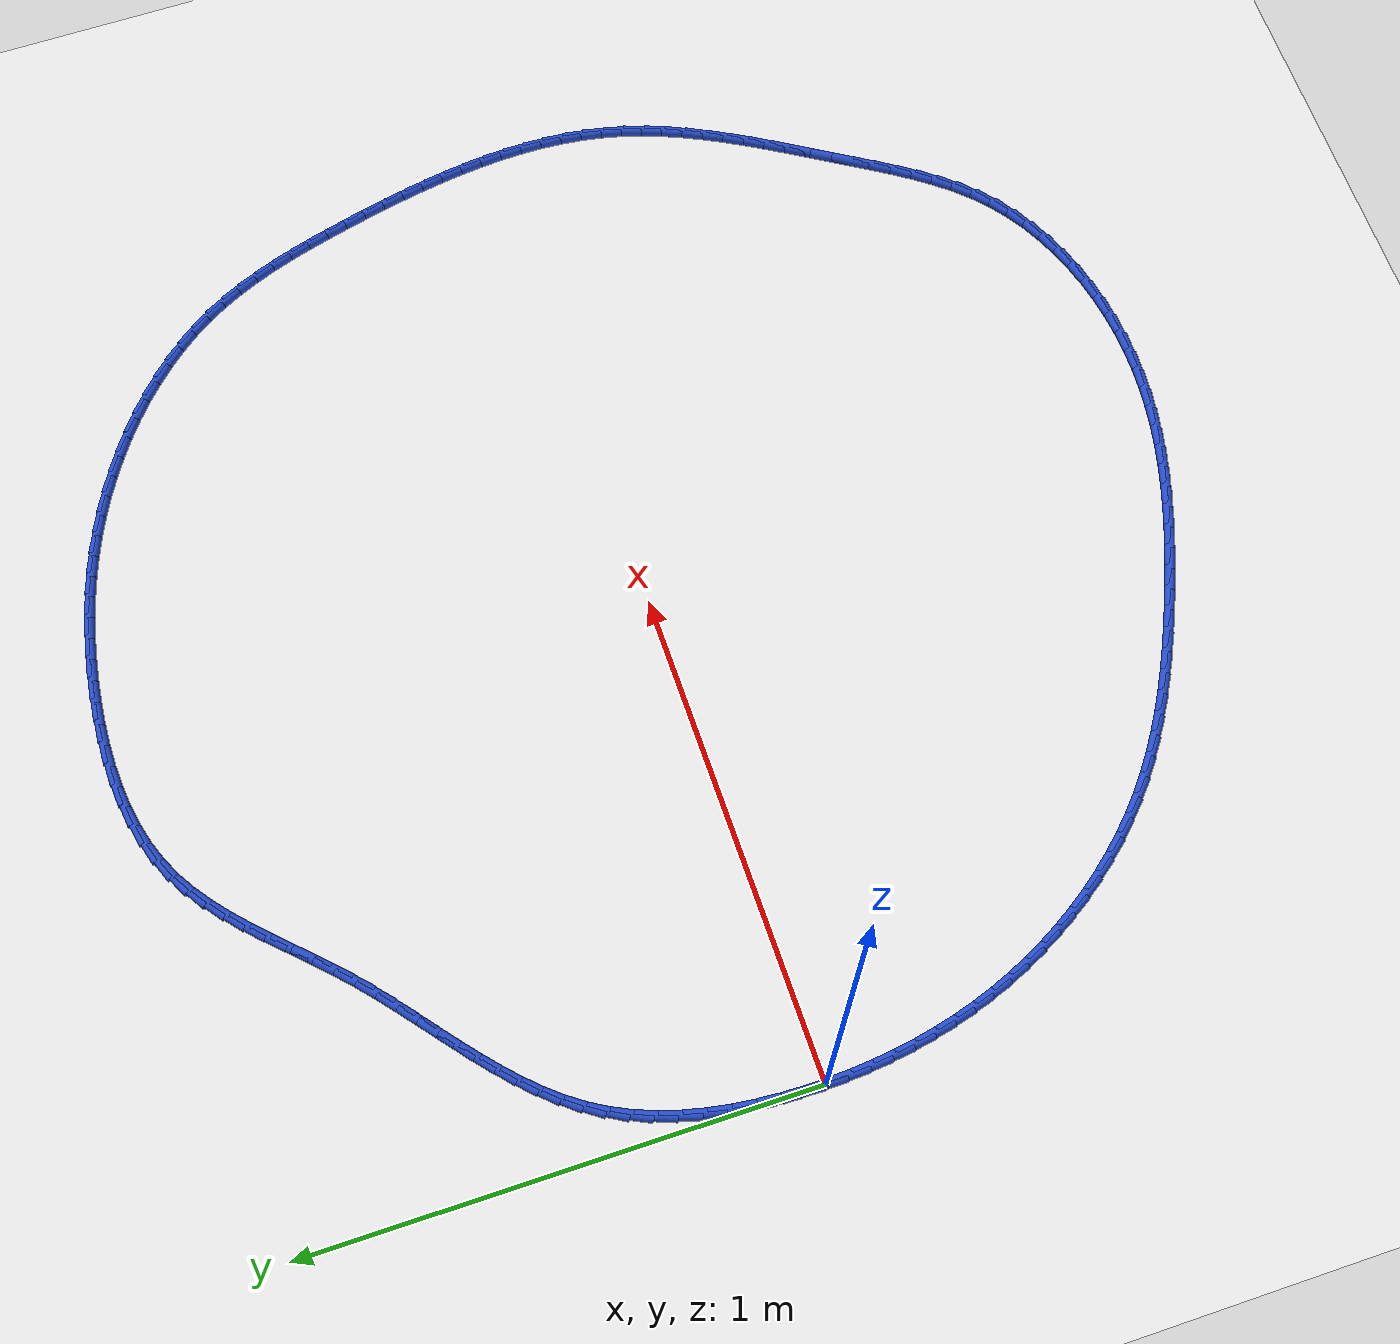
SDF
<sdf version="1.6">
 <world name="default">
  <light name="sun" type="directional">
   <pose>0 0 10 0 -0 0</pose>
   <diffuse>0.8 0.8 0.8 1</diffuse>
   <specular>0.2 0.2 0.2 1</specular>
   <attenuation>
    <range>1000</range>
    <constant>0.9</constant>
    <linear>0.01</linear>
    <quadratic>0.001</quadratic>
   </attenuation>
   <direction>-0.5 0.1 -0.9</direction>
  </light>
  <model name="ground_plane">
   <static>1</static>
   <link name="link">
    <collision name="collision">
     <geometry><plane><normal>0 0 1</normal><size>100 100</size></plane></geometry>
     <surface><friction><ode><mu>100</mu><mu2>50</mu2></ode></friction></surface>
    </collision>
    <visual name="visual">
     <cast_shadows>0</cast_shadows>
     <geometry><plane><normal>0 0 1</normal><size>100 100</size></plane></geometry>
     <material>
      <script><uri>file://media/materials/scripts/gazebo.material</uri><name>Gazebo/WhiteGlow</name></script>
     </material>
    </visual>
   </link>
  </model>
  <gravity>0 0 -9.8</gravity>
  <magnetic_field>6e-06 2.3e-05 -4.2e-05</magnetic_field>
  <atmosphere type="adiabatic"/>
  <physics name="default_physics" default="0" type="ode">
   <max_step_size>0.001</max_step_size>
   <real_time_factor>1</real_time_factor>
   <real_time_update_rate>1000</real_time_update_rate>
  </physics>
  <scene><ambient>0.4 0.4 0.4 1</ambient><background>0.7 0.7 0.7 1</background><shadows>1</shadows></scene>
  <spherical_coordinates>
   <surface_model>EARTH_WGS84</surface_model>
   <latitude_deg>0</latitude_deg>
   <longitude_deg>0</longitude_deg>
   <elevation>0</elevation>
   <heading_deg>0</heading_deg>
  </spherical_coordinates>
  <model name="line">
   <link name="link_0">
    <pose>3.469446951953614e-18 -2.7755575615628914e-17 0.01 0 1.57 -1.5662328181608505</pose>
    <collision name="collision">
     <geometry><cylinder><radius>0.01</radius><length>0.08</length></cylinder></geometry>
    </collision>
    <visual name="visual">
     <material>
      <script><name>Gazebo/Blue</name><uri>file://media/materials/scripts/gazebo.material</uri></script>
     </material>
     <geometry><cylinder><radius>0.01</radius><length>0.08</length></cylinder></geometry>
    </visual>
   </link>
   <link name="link_1">
    <pose>-0.00020602253707400727 0.04514533079947657 0.01 0 1.57 1.5365275692211684</pose>
    <collision name="collision">
     <geometry><cylinder><radius>0.01</radius><length>0.08</length></cylinder></geometry>
    </collision>
    <visual name="visual">
     <material>
      <script><name>Gazebo/Blue</name><uri>file://media/materials/scripts/gazebo.material</uri></script>
     </material>
     <geometry><cylinder><radius>0.01</radius><length>0.08</length></cylinder></geometry>
    </visual>
   </link>
   <link name="link_2">
    <pose>0.0013460004159330614 0.09041733588694323 0.01 0 1.57 1.4938808284677962</pose>
    <collision name="collision">
     <geometry><cylinder><radius>0.01</radius><length>0.08</length></cylinder></geometry>
    </collision>
    <visual name="visual">
     <material>
      <script><name>Gazebo/Blue</name><uri>file://media/materials/scripts/gazebo.material</uri></script>
     </material>
     <geometry><cylinder><radius>0.01</radius><length>0.08</length></cylinder></geometry>
    </visual>
   </link>
   <link name="link_3">
    <pose>0.00482324214725611 0.13553674598285181 0.01 0 1.57 1.446800699411635</pose>
    <collision name="collision">
     <geometry><cylinder><radius>0.01</radius><length>0.08</length></cylinder></geometry>
    </collision>
    <visual name="visual">
     <material>
      <script><name>Gazebo/Blue</name><uri>file://media/materials/scripts/gazebo.material</uri></script>
     </material>
     <geometry><cylinder><radius>0.01</radius><length>0.08</length></cylinder></geometry>
    </visual>
   </link>
   <link name="link_4">
    <pose>0.010392875945130043 0.18022429180765426 0.01 0 1.57 1.3946104873315452</pose>
    <collision name="collision">
     <geometry><cylinder><radius>0.01</radius><length>0.08</length></cylinder></geometry>
    </collision>
    <visual name="visual">
     <material>
      <script><name>Gazebo/Blue</name><uri>file://media/materials/scripts/gazebo.material</uri></script>
     </material>
     <geometry><cylinder><radius>0.01</radius><length>0.08</length></cylinder></geometry>
    </visual>
   </link>
   <link name="link_5">
    <pose>0.01822207509778976 0.22420070408180257 0.01 0 1.57 1.3365870525976995</pose>
    <collision name="collision">
     <geometry><cylinder><radius>0.01</radius><length>0.08</length></cylinder></geometry>
    </collision>
    <visual name="visual">
     <material>
      <script><name>Gazebo/Blue</name><uri>file://media/materials/scripts/gazebo.material</uri></script>
     </material>
     <geometry><cylinder><radius>0.01</radius><length>0.08</length></cylinder></geometry>
    </visual>
   </link>
   <link name="link_6">
    <pose>0.02847801289347018 0.2671867135257487 0.01 0 1.57 1.2719896750110322</pose>
    <collision name="collision">
     <geometry><cylinder><radius>0.01</radius><length>0.08</length></cylinder></geometry>
    </collision>
    <visual name="visual">
     <material>
      <script><name>Gazebo/Blue</name><uri>file://media/materials/scripts/gazebo.material</uri></script>
     </material>
     <geometry><cylinder><radius>0.01</radius><length>0.08</length></cylinder></geometry>
    </visual>
   </link>
   <link name="link_7">
    <pose>0.041327862620406206 0.3089030508599446 0.01 0 1.57 1.200115232319605</pose>
    <collision name="collision">
     <geometry><cylinder><radius>0.01</radius><length>0.08</length></cylinder></geometry>
    </collision>
    <visual name="visual">
     <material>
      <script><name>Gazebo/Blue</name><uri>file://media/materials/scripts/gazebo.material</uri></script>
     </material>
     <geometry><cylinder><radius>0.01</radius><length>0.08</length></cylinder></geometry>
    </visual>
   </link>
   <link name="link_8">
    <pose>0.056938797566832726 0.34907044680484217 0.01 0 1.57 1.120389181391767</pose>
    <collision name="collision">
     <geometry><cylinder><radius>0.01</radius><length>0.08</length></cylinder></geometry>
    </collision>
    <visual name="visual">
     <material>
      <script><name>Gazebo/Blue</name><uri>file://media/materials/scripts/gazebo.material</uri></script>
     </material>
     <geometry><cylinder><radius>0.01</radius><length>0.08</length></cylinder></geometry>
    </visual>
   </link>
   <link name="link_9">
    <pose>0.07547799102098467 0.38740963208089335 0.01 0 1.57 1.0328212205551348</pose>
    <collision name="collision">
     <geometry><cylinder><radius>0.01</radius><length>0.08</length></cylinder></geometry>
    </collision>
    <visual name="visual">
     <material>
      <script><name>Gazebo/Blue</name><uri>file://media/materials/scripts/gazebo.material</uri></script>
     </material>
     <geometry><cylinder><radius>0.01</radius><length>0.08</length></cylinder></geometry>
    </visual>
   </link>
   <link name="link_10">
    <pose>0.09710295406298641 0.42365174749847884 0.01 0 1.57 0.9461803319421407</pose>
    <collision name="collision">
     <geometry><cylinder><radius>0.01</radius><length>0.08</length></cylinder></geometry>
    </collision>
    <visual name="visual">
     <material>
      <script><name>Gazebo/Blue</name><uri>file://media/materials/scripts/gazebo.material</uri></script>
     </material>
     <geometry><cylinder><radius>0.01</radius><length>0.08</length></cylinder></geometry>
    </visual>
   </link>
   <link name="link_11">
    <pose>0.1217196770446741 0.45779892300115727 0.01 0 1.57 0.8707524983348643</pose>
    <collision name="collision">
     <geometry><cylinder><radius>0.01</radius><length>0.08</length></cylinder></geometry>
    </collision>
    <visual name="visual">
     <material>
      <script><name>Gazebo/Blue</name><uri>file://media/materials/scripts/gazebo.material</uri></script>
     </material>
     <geometry><cylinder><radius>0.01</radius><length>0.08</length></cylinder></geometry>
    </visual>
   </link>
   <link name="link_12">
    <pose>0.14896519378176706 0.49014306305357924 0.01 0 1.57 0.8077489555728229</pose>
    <collision name="collision">
     <geometry><cylinder><radius>0.01</radius><length>0.08</length></cylinder></geometry>
    </collision>
    <visual name="visual">
     <material>
      <script><name>Gazebo/Blue</name><uri>file://media/materials/scripts/gazebo.material</uri></script>
     </material>
     <geometry><cylinder><radius>0.01</radius><length>0.08</length></cylinder></geometry>
    </visual>
   </link>
   <link name="link_13">
    <pose>0.1784633838088167 0.520990244579563 0.01 0 1.57 0.7572487342943846</pose>
    <collision name="collision">
     <geometry><cylinder><radius>0.01</radius><length>0.08</length></cylinder></geometry>
    </collision>
    <visual name="visual">
     <material>
      <script><name>Gazebo/Blue</name><uri>file://media/materials/scripts/gazebo.material</uri></script>
     </material>
     <geometry><cylinder><radius>0.01</radius><length>0.08</length></cylinder></geometry>
    </visual>
   </link>
   <link name="link_14">
    <pose>0.20983812666037432 0.5506465445029266 0.01 0 1.57 0.7189284821755045</pose>
    <collision name="collision">
     <geometry><cylinder><radius>0.01</radius><length>0.08</length></cylinder></geometry>
    </collision>
    <visual name="visual">
     <material>
      <script><name>Gazebo/Blue</name><uri>file://media/materials/scripts/gazebo.material</uri></script>
     </material>
     <geometry><cylinder><radius>0.01</radius><length>0.08</length></cylinder></geometry>
    </visual>
   </link>
   <link name="link_15">
    <pose>0.24271330187099135 0.5794180397474883 0.01 0 1.57 0.6923008136913837</pose>
    <collision name="collision">
     <geometry><cylinder><radius>0.01</radius><length>0.08</length></cylinder></geometry>
    </collision>
    <visual name="visual">
     <material>
      <script><name>Gazebo/Blue</name><uri>file://media/materials/scripts/gazebo.material</uri></script>
     </material>
     <geometry><cylinder><radius>0.01</radius><length>0.08</length></cylinder></geometry>
    </visual>
   </link>
   <link name="link_16">
    <pose>0.2767127889752188 0.6076108072370656 0.01 0 1.57 0.6768776904252869</pose>
    <collision name="collision">
     <geometry><cylinder><radius>0.01</radius><length>0.08</length></cylinder></geometry>
    </collision>
    <visual name="visual">
     <material>
      <script><name>Gazebo/Blue</name><uri>file://media/materials/scripts/gazebo.material</uri></script>
     </material>
     <geometry><cylinder><radius>0.01</radius><length>0.08</length></cylinder></geometry>
    </visual>
   </link>
   <link name="link_17">
    <pose>0.3114604675076083 0.6355309238954772 0.01 0 1.57 0.6722661655963784</pose>
    <collision name="collision">
     <geometry><cylinder><radius>0.01</radius><length>0.08</length></cylinder></geometry>
    </collision>
    <visual name="visual">
     <material>
      <script><name>Gazebo/Blue</name><uri>file://media/materials/scripts/gazebo.material</uri></script>
     </material>
     <geometry><cylinder><radius>0.01</radius><length>0.08</length></cylinder></geometry>
    </visual>
   </link>
   <link name="link_18">
    <pose>0.34658021700271086 0.6634844666465405 0.01 0 1.57 0.6782125351929353</pose>
    <collision name="collision">
     <geometry><cylinder><radius>0.01</radius><length>0.08</length></cylinder></geometry>
    </collision>
    <visual name="visual">
     <material>
      <script><name>Gazebo/Blue</name><uri>file://media/materials/scripts/gazebo.material</uri></script>
     </material>
     <geometry><cylinder><radius>0.01</radius><length>0.08</length></cylinder></geometry>
    </visual>
   </link>
   <link name="link_19">
    <pose>0.3816959169950781 0.6917775124140739 0.01 0 1.57 0.6946082987009818</pose>
    <collision name="collision">
     <geometry><cylinder><radius>0.01</radius><length>0.08</length></cylinder></geometry>
    </collision>
    <visual name="visual">
     <material>
      <script><name>Gazebo/Blue</name><uri>file://media/materials/scripts/gazebo.material</uri></script>
     </material>
     <geometry><cylinder><radius>0.01</radius><length>0.08</length></cylinder></geometry>
    </visual>
   </link>
   <link name="link_20">
    <pose>0.41643144701926105 0.7207161381218956 0.01 0 1.57 0.7214649411585046</pose>
    <collision name="collision">
     <geometry><cylinder><radius>0.01</radius><length>0.08</length></cylinder></geometry>
    </collision>
    <visual name="visual">
     <material>
      <script><name>Gazebo/Blue</name><uri>file://media/materials/scripts/gazebo.material</uri></script>
     </material>
     <geometry><cylinder><radius>0.01</radius><length>0.08</length></cylinder></geometry>
    </visual>
   </link>
   <link name="link_21">
    <pose>0.45041068660981143 0.7506064206938237 0.01 0 1.57 0.7559417604104025</pose>
    <collision name="collision">
     <geometry><cylinder><radius>0.01</radius><length>0.08</length></cylinder></geometry>
    </collision>
    <visual name="visual">
     <material>
      <script><name>Gazebo/Blue</name><uri>file://media/materials/scripts/gazebo.material</uri></script>
     </material>
     <geometry><cylinder><radius>0.01</radius><length>0.08</length></cylinder></geometry>
    </visual>
   </link>
   <link name="link_22">
    <pose>0.483343160799513 0.7816537351755948 0.01 0 1.57 0.7818930835358702</pose>
    <collision name="collision">
     <geometry><cylinder><radius>0.01</radius><length>0.08</length></cylinder></geometry>
    </collision>
    <visual name="visual">
     <material>
      <script><name>Gazebo/Blue</name><uri>file://media/materials/scripts/gazebo.material</uri></script>
     </material>
     <geometry><cylinder><radius>0.01</radius><length>0.08</length></cylinder></geometry>
    </visual>
   </link>
   <link name="link_23">
    <pose>0.5154157075397474 0.8135022326335528 0.01 0 1.57 0.7937970196566747</pose>
    <collision name="collision">
     <geometry><cylinder><radius>0.01</radius><length>0.08</length></cylinder></geometry>
    </collision>
    <visual name="visual">
     <material>
      <script><name>Gazebo/Blue</name><uri>file://media/materials/scripts/gazebo.material</uri></script>
     </material>
     <geometry><cylinder><radius>0.01</radius><length>0.08</length></cylinder></geometry>
    </visual>
   </link>
   <link name="link_24">
    <pose>0.5469804626781769 0.8456017070581688 0.01 0 1.57 0.791580660811204</pose>
    <collision name="collision">
     <geometry><cylinder><radius>0.01</radius><length>0.08</length></cylinder></geometry>
    </collision>
    <visual name="visual">
     <material>
      <script><name>Gazebo/Blue</name><uri>file://media/materials/scripts/gazebo.material</uri></script>
     </material>
     <geometry><cylinder><radius>0.01</radius><length>0.08</length></cylinder></geometry>
    </visual>
   </link>
   <link name="link_25">
    <pose>0.5783897227309726 0.8774017635260645 0.01 0 1.57 0.7749149056330398</pose>
    <collision name="collision">
     <geometry><cylinder><radius>0.01</radius><length>0.08</length></cylinder></geometry>
    </collision>
    <visual name="visual">
     <material>
      <script><name>Gazebo/Blue</name><uri>file://media/materials/scripts/gazebo.material</uri></script>
     </material>
     <geometry><cylinder><radius>0.01</radius><length>0.08</length></cylinder></geometry>
    </visual>
   </link>
   <link name="link_26">
    <pose>0.6099957842143057 0.908352007113862 0.01 0 1.57 0.7432043502115773</pose>
    <collision name="collision">
     <geometry><cylinder><radius>0.01</radius><length>0.08</length></cylinder></geometry>
    </collision>
    <visual name="visual">
     <material>
      <script><name>Gazebo/Blue</name><uri>file://media/materials/scripts/gazebo.material</uri></script>
     </material>
     <geometry><cylinder><radius>0.01</radius><length>0.08</length></cylinder></geometry>
    </visual>
   </link>
   <link name="link_27">
    <pose>0.6421509436443478 0.9379020428981834 0.01 0 1.57 0.6956713560132353</pose>
    <collision name="collision">
     <geometry><cylinder><radius>0.01</radius><length>0.08</length></cylinder></geometry>
    </collision>
    <visual name="visual">
     <material>
      <script><name>Gazebo/Blue</name><uri>file://media/materials/scripts/gazebo.material</uri></script>
     </material>
     <geometry><cylinder><radius>0.01</radius><length>0.08</length></cylinder></geometry>
    </visual>
   </link>
   <link name="link_28">
    <pose>0.6752074975372702 0.9655014759556512 0.01 0 1.57 0.6315649234335238</pose>
    <collision name="collision">
     <geometry><cylinder><radius>0.01</radius><length>0.08</length></cylinder></geometry>
    </collision>
    <visual name="visual">
     <material>
      <script><name>Gazebo/Blue</name><uri>file://media/materials/scripts/gazebo.material</uri></script>
     </material>
     <geometry><cylinder><radius>0.01</radius><length>0.08</length></cylinder></geometry>
    </visual>
   </link>
   <link name="link_29">
    <pose>0.709517742409244 0.990599911362887 0.01 0 1.57 0.5505383714419325</pose>
    <collision name="collision">
     <geometry><cylinder><radius>0.01</radius><length>0.08</length></cylinder></geometry>
    </collision>
    <visual name="visual">
     <material>
      <script><name>Gazebo/Blue</name><uri>file://media/materials/scripts/gazebo.material</uri></script>
     </material>
     <geometry><cylinder><radius>0.01</radius><length>0.08</length></cylinder></geometry>
    </visual>
   </link>
   <link name="link_30">
    <pose>0.7454339747764408 1.0126469541965135 0.01 0 1.57 0.45357030850402397</pose>
    <collision name="collision">
     <geometry><cylinder><radius>0.01</radius><length>0.08</length></cylinder></geometry>
    </collision>
    <visual name="visual">
     <material>
      <script><name>Gazebo/Blue</name><uri>file://media/materials/scripts/gazebo.material</uri></script>
     </material>
     <geometry><cylinder><radius>0.01</radius><length>0.08</length></cylinder></geometry>
    </visual>
   </link>
   <link name="link_31">
    <pose>0.7832985049923746 1.03110462922118 0.01 0 1.57 0.35332833808266917</pose>
    <collision name="collision">
     <geometry><cylinder><radius>0.01</radius><length>0.08</length></cylinder></geometry>
    </collision>
    <visual name="visual">
     <material>
      <script><name>Gazebo/Blue</name><uri>file://media/materials/scripts/gazebo.material</uri></script>
     </material>
     <geometry><cylinder><radius>0.01</radius><length>0.08</length></cylinder></geometry>
    </visual>
   </link>
   <link name="link_32">
    <pose>0.8231565381078694 1.0458044680178495 0.01 0 1.57 0.26318274665005087</pose>
    <collision name="collision">
     <geometry><cylinder><radius>0.01</radius><length>0.08</length></cylinder></geometry>
    </collision>
    <visual name="visual">
     <material>
      <script><name>Gazebo/Blue</name><uri>file://media/materials/scripts/gazebo.material</uri></script>
     </material>
     <geometry><cylinder><radius>0.01</radius><length>0.08</length></cylinder></geometry>
    </visual>
   </link>
   <link name="link_33">
    <pose>0.8647130513239211 1.0570011400531898 0.01 0 1.57 0.18354505986909575</pose>
    <collision name="collision">
     <geometry><cylinder><radius>0.01</radius><length>0.08</length></cylinder></geometry>
    </collision>
    <visual name="visual">
     <material>
      <script><name>Gazebo/Blue</name><uri>file://media/materials/scripts/gazebo.material</uri></script>
     </material>
     <geometry><cylinder><radius>0.01</radius><length>0.08</length></cylinder></geometry>
    </visual>
   </link>
   <link name="link_34">
    <pose>0.907654361479108 1.0649725224951287 0.01 0 1.57 0.11365696003977273</pose>
    <collision name="collision">
     <geometry><cylinder><radius>0.01</radius><length>0.08</length></cylinder></geometry>
    </collision>
    <visual name="visual">
     <material>
      <script><name>Gazebo/Blue</name><uri>file://media/materials/scripts/gazebo.material</uri></script>
     </material>
     <geometry><cylinder><radius>0.01</radius><length>0.08</length></cylinder></geometry>
    </visual>
   </link>
   <link name="link_35">
    <pose>0.9516667854120098 1.0699964925115943 0.01 0 1.57 0.05254133254348595</pose>
    <collision name="collision">
     <geometry><cylinder><radius>0.01</radius><length>0.08</length></cylinder></geometry>
    </collision>
    <visual name="visual">
     <material>
      <script><name>Gazebo/Blue</name><uri>file://media/materials/scripts/gazebo.material</uri></script>
     </material>
     <geometry><cylinder><radius>0.01</radius><length>0.08</length></cylinder></geometry>
    </visual>
   </link>
   <link name="link_36">
    <pose>0.9964366399612051 1.0723509272705143 0.01 0 1.57 -0.0008232770811992697</pose>
    <collision name="collision">
     <geometry><cylinder><radius>0.01</radius><length>0.08</length></cylinder></geometry>
    </collision>
    <visual name="visual">
     <material>
      <script><name>Gazebo/Blue</name><uri>file://media/materials/scripts/gazebo.material</uri></script>
     </material>
     <geometry><cylinder><radius>0.01</radius><length>0.08</length></cylinder></geometry>
    </visual>
   </link>
   <link name="link_37">
    <pose>1.041650241965273 1.072313703939816 0.01 0 1.57 -0.04740227471176772</pose>
    <collision name="collision">
     <geometry><cylinder><radius>0.01</radius><length>0.08</length></cylinder></geometry>
    </collision>
    <visual name="visual">
     <material>
      <script><name>Gazebo/Blue</name><uri>file://media/materials/scripts/gazebo.material</uri></script>
     </material>
     <geometry><cylinder><radius>0.01</radius><length>0.08</length></cylinder></geometry>
    </visual>
   </link>
   <link name="link_38">
    <pose>1.0869939082627924 1.0701626996874283 0.01 0 1.57 -0.0880556673157361</pose>
    <collision name="collision">
     <geometry><cylinder><radius>0.01</radius><length>0.08</length></cylinder></geometry>
    </collision>
    <visual name="visual">
     <material>
      <script><name>Gazebo/Blue</name><uri>file://media/materials/scripts/gazebo.material</uri></script>
     </material>
     <geometry><cylinder><radius>0.01</radius><length>0.08</length></cylinder></geometry>
    </visual>
   </link>
   <link name="link_39">
    <pose>1.1321539556923421 1.0661757916812784 0.01 0 1.57 -0.12354309175123841</pose>
    <collision name="collision">
     <geometry><cylinder><radius>0.01</radius><length>0.08</length></cylinder></geometry>
    </collision>
    <visual name="visual">
     <material>
      <script><name>Gazebo/Blue</name><uri>file://media/materials/scripts/gazebo.material</uri></script>
     </material>
     <geometry><cylinder><radius>0.01</radius><length>0.08</length></cylinder></geometry>
    </visual>
   </link>
   <link name="link_40">
    <pose>1.1768179660798448 1.060629616095258 0.01 0 1.57 -0.15659754596443135</pose>
    <collision name="collision">
     <geometry><cylinder><radius>0.01</radius><length>0.08</length></cylinder></geometry>
    </collision>
    <visual name="visual">
     <material>
      <script><name>Gazebo/Blue</name><uri>file://media/materials/scripts/gazebo.material</uri></script>
     </material>
     <geometry><cylinder><radius>0.01</radius><length>0.08</length></cylinder></geometry>
    </visual>
   </link>
   <link name="link_41">
    <pose>1.2207896125474373 1.0536869197374448 0.01 0 1.57 -0.19121898460909753</pose>
    <collision name="collision">
     <geometry><cylinder><radius>0.01</radius><length>0.08</length></cylinder></geometry>
    </collision>
    <visual name="visual">
     <material>
      <script><name>Gazebo/Blue</name><uri>file://media/materials/scripts/gazebo.material</uri></script>
     </material>
     <geometry><cylinder><radius>0.01</radius><length>0.08</length></cylinder></geometry>
    </visual>
   </link>
   <link name="link_42">
    <pose>1.264080466787545 1.0453064941057777 0.01 0 1.57 -0.22768503858807543</pose>
    <collision name="collision">
     <geometry><cylinder><radius>0.01</radius><length>0.08</length></cylinder></geometry>
    </collision>
    <visual name="visual">
     <material>
      <script><name>Gazebo/Blue</name><uri>file://media/materials/scripts/gazebo.material</uri></script>
     </material>
     <geometry><cylinder><radius>0.01</radius><length>0.08</length></cylinder></geometry>
    </visual>
   </link>
   <link name="link_43">
    <pose>1.3067237047537577 1.0354259362100404 0.01 0 1.57 -0.2658244442742351</pose>
    <collision name="collision">
     <geometry><cylinder><radius>0.01</radius><length>0.08</length></cylinder></geometry>
    </collision>
    <visual name="visual">
     <material>
      <script><name>Gazebo/Blue</name><uri>file://media/materials/scripts/gazebo.material</uri></script>
     </material>
     <geometry><cylinder><radius>0.01</radius><length>0.08</length></cylinder></geometry>
    </visual>
   </link>
   <link name="link_44">
    <pose>1.3487525023996623 1.0239828430600149 0.01 0 1.57 -0.30542547260663827</pose>
    <collision name="collision">
     <geometry><cylinder><radius>0.01</radius><length>0.08</length></cylinder></geometry>
    </collision>
    <visual name="visual">
     <material>
      <script><name>Gazebo/Blue</name><uri>file://media/materials/scripts/gazebo.material</uri></script>
     </material>
     <geometry><cylinder><radius>0.01</radius><length>0.08</length></cylinder></geometry>
    </visual>
   </link>
   <link name="link_45">
    <pose>1.3902000356788489 1.0109148116654851 0.01 0 1.57 -0.3462387991575919</pose>
    <collision name="collision">
     <geometry><cylinder><radius>0.01</radius><length>0.08</length></cylinder></geometry>
    </collision>
    <visual name="visual">
     <material>
      <script><name>Gazebo/Blue</name><uri>file://media/materials/scripts/gazebo.material</uri></script>
     </material>
     <geometry><cylinder><radius>0.01</radius><length>0.08</length></cylinder></geometry>
    </visual>
   </link>
   <link name="link_46">
    <pose>1.4310994805449044 0.9961594390362342 0.01 0 1.57 -0.38798292365209136</pose>
    <collision name="collision">
     <geometry><cylinder><radius>0.01</radius><length>0.08</length></cylinder></geometry>
    </collision>
    <visual name="visual">
     <material>
      <script><name>Gazebo/Blue</name><uri>file://media/materials/scripts/gazebo.material</uri></script>
     </material>
     <geometry><cylinder><radius>0.01</radius><length>0.08</length></cylinder></geometry>
    </visual>
   </link>
   <link name="link_47">
    <pose>1.4714840129514173 0.9796543221820447 0.01 0 1.57 -0.4303517544796513</pose>
    <collision name="collision">
     <geometry><cylinder><radius>0.01</radius><length>0.08</length></cylinder></geometry>
    </collision>
    <visual name="visual">
     <material>
      <script><name>Gazebo/Blue</name><uri>file://media/materials/scripts/gazebo.material</uri></script>
     </material>
     <geometry><cylinder><radius>0.01</radius><length>0.08</length></cylinder></geometry>
    </visual>
   </link>
   <link name="link_48">
    <pose>1.5113864995676047 0.9613372120985697 0.01 0 1.57 -0.4730434057449655</pose>
    <collision name="collision">
     <geometry><cylinder><radius>0.01</radius><length>0.08</length></cylinder></geometry>
    </collision>
    <visual name="visual">
     <material>
      <script><name>Gazebo/Blue</name><uri>file://media/materials/scripts/gazebo.material</uri></script>
     </material>
     <geometry><cylinder><radius>0.01</radius><length>0.08</length></cylinder></geometry>
    </visual>
   </link>
   <link name="link_49">
    <pose>1.5507772178040684 0.9411770215933531 0.01 0 1.57 -0.5161218047111916</pose>
    <collision name="collision">
     <geometry><cylinder><radius>0.01</radius><length>0.08</length></cylinder></geometry>
    </collision>
    <visual name="visual">
     <material>
      <script><name>Gazebo/Blue</name><uri>file://media/materials/scripts/gazebo.material</uri></script>
     </material>
     <geometry><cylinder><radius>0.01</radius><length>0.08</length></cylinder></geometry>
    </visual>
   </link>
   <link name="link_50">
    <pose>1.5894882355418278 0.9192114749514636 0.01 0 1.57 -0.5599455992413617</pose>
    <collision name="collision">
     <geometry><cylinder><radius>0.01</radius><length>0.08</length></cylinder></geometry>
    </collision>
    <visual name="visual">
     <material>
      <script><name>Gazebo/Blue</name><uri>file://media/materials/scripts/gazebo.material</uri></script>
     </material>
     <geometry><cylinder><radius>0.01</radius><length>0.08</length></cylinder></geometry>
    </visual>
   </link>
   <link name="link_51">
    <pose>1.6273331404596965 0.8954874973431952 0.01 0 1.57 -0.6048799009087822</pose>
    <collision name="collision">
     <geometry><cylinder><radius>0.01</radius><length>0.08</length></cylinder></geometry>
    </collision>
    <visual name="visual">
     <material>
      <script><name>Gazebo/Blue</name><uri>file://media/materials/scripts/gazebo.material</uri></script>
     </material>
     <geometry><cylinder><radius>0.01</radius><length>0.08</length></cylinder></geometry>
    </visual>
   </link>
   <link name="link_52">
    <pose>1.6641255202364884 0.8700520139388414 0.01 0 1.57 -0.6512853833089659</pose>
    <collision name="collision">
     <geometry><cylinder><radius>0.01</radius><length>0.08</length></cylinder></geometry>
    </collision>
    <visual name="visual">
     <material>
      <script><name>Gazebo/Blue</name><uri>file://media/materials/scripts/gazebo.material</uri></script>
     </material>
     <geometry><cylinder><radius>0.01</radius><length>0.08</length></cylinder></geometry>
    </visual>
   </link>
   <link name="link_53">
    <pose>1.6996789625510178 0.8429519499086955 0.01 0 1.57 -0.6995202694699366</pose>
    <collision name="collision">
     <geometry><cylinder><radius>0.01</radius><length>0.08</length></cylinder></geometry>
    </collision>
    <visual name="visual">
     <material>
      <script><name>Gazebo/Blue</name><uri>file://media/materials/scripts/gazebo.material</uri></script>
     </material>
     <geometry><cylinder><radius>0.01</radius><length>0.08</length></cylinder></geometry>
    </visual>
   </link>
   <link name="link_54">
    <pose>1.7338070550820992 0.8142342304230514 0.01 0 1.57 -0.7499399247818923</pose>
    <collision name="collision">
     <geometry><cylinder><radius>0.01</radius><length>0.08</length></cylinder></geometry>
    </collision>
    <visual name="visual">
     <material>
      <script><name>Gazebo/Blue</name><uri>file://media/materials/scripts/gazebo.material</uri></script>
     </material>
     <geometry><cylinder><radius>0.01</radius><length>0.08</length></cylinder></geometry>
    </visual>
   </link>
   <link name="link_55">
    <pose>1.7663233855085465 0.7839457806522034 0.01 0 1.57 -0.802893446704945</pose>
    <collision name="collision">
     <geometry><cylinder><radius>0.01</radius><length>0.08</length></cylinder></geometry>
    </collision>
    <visual name="visual">
     <material>
      <script><name>Gazebo/Blue</name><uri>file://media/materials/scripts/gazebo.material</uri></script>
     </material>
     <geometry><cylinder><radius>0.01</radius><length>0.08</length></cylinder></geometry>
    </visual>
   </link>
   <link name="link_56">
    <pose>1.797041541509173 0.7521335257664444 0.01 0 1.57 -0.8587164714265515</pose>
    <collision name="collision">
     <geometry><cylinder><radius>0.01</radius><length>0.08</length></cylinder></geometry>
    </collision>
    <visual name="visual">
     <material>
      <script><name>Gazebo/Blue</name><uri>file://media/materials/scripts/gazebo.material</uri></script>
     </material>
     <geometry><cylinder><radius>0.01</radius><length>0.08</length></cylinder></geometry>
    </visual>
   </link>
   <link name="link_57">
    <pose>1.8257751107627938 0.7188443909360683 0.01 0 1.57 -0.9177193167012746</pose>
    <collision name="collision">
     <geometry><cylinder><radius>0.01</radius><length>0.08</length></cylinder></geometry>
    </collision>
    <visual name="visual">
     <material>
      <script><name>Gazebo/Blue</name><uri>file://media/materials/scripts/gazebo.material</uri></script>
     </material>
     <geometry><cylinder><radius>0.01</radius><length>0.08</length></cylinder></geometry>
    </visual>
   </link>
   <link name="link_58">
    <pose>1.8523376809482233 0.6841253013313688 0.01 0 1.57 -0.9801696436704599</pose>
    <collision name="collision">
     <geometry><cylinder><radius>0.01</radius><length>0.08</length></cylinder></geometry>
    </collision>
    <visual name="visual">
     <material>
      <script><name>Gazebo/Blue</name><uri>file://media/materials/scripts/gazebo.material</uri></script>
     </material>
     <geometry><cylinder><radius>0.01</radius><length>0.08</length></cylinder></geometry>
    </visual>
   </link>
   <link name="link_59">
    <pose>1.8765428397442745 0.6480231821226398 0.01 0 1.57 -1.0456846434320672</pose>
    <collision name="collision">
     <geometry><cylinder><radius>0.01</radius><length>0.08</length></cylinder></geometry>
    </collision>
    <visual name="visual">
     <material>
      <script><name>Gazebo/Blue</name><uri>file://media/materials/scripts/gazebo.material</uri></script>
     </material>
     <geometry><cylinder><radius>0.01</radius><length>0.08</length></cylinder></geometry>
    </visual>
   </link>
   <link name="link_60">
    <pose>1.898230741698793 0.6105895382829252 0.01 0 1.57 -1.1080162044766644</pose>
    <collision name="collision">
     <geometry><cylinder><radius>0.01</radius><length>0.08</length></cylinder></geometry>
    </collision>
    <visual name="visual">
     <material>
      <script><name>Gazebo/Blue</name><uri>file://media/materials/scripts/gazebo.material</uri></script>
     </material>
     <geometry><cylinder><radius>0.01</radius><length>0.08</length></cylinder></geometry>
    </visual>
   </link>
   <link name="link_61">
    <pose>1.9175215310709175 0.571924141581344 0.01 0 1.57 -1.1629761503358158</pose>
    <collision name="collision">
     <geometry><cylinder><radius>0.01</radius><length>0.08</length></cylinder></geometry>
    </collision>
    <visual name="visual">
     <material>
      <script><name>Gazebo/Blue</name><uri>file://media/materials/scripts/gazebo.material</uri></script>
     </material>
     <geometry><cylinder><radius>0.01</radius><length>0.08</length></cylinder></geometry>
    </visual>
   </link>
   <link name="link_62">
    <pose>1.9347031727631612 0.5321556940099638 0.01 0 1.57 -1.2102122241353317</pose>
    <collision name="collision">
     <geometry><cylinder><radius>0.01</radius><length>0.08</length></cylinder></geometry>
    </collision>
    <visual name="visual">
     <material>
      <script><name>Gazebo/Blue</name><uri>file://media/materials/scripts/gazebo.material</uri></script>
     </material>
     <geometry><cylinder><radius>0.01</radius><length>0.08</length></cylinder></geometry>
    </visual>
   </link>
   <link name="link_63">
    <pose>1.950065905365327 0.49141328951668645 0.01 0 1.57 -1.2496596518327214</pose>
    <collision name="collision">
     <geometry><cylinder><radius>0.01</radius><length>0.08</length></cylinder></geometry>
    </collision>
    <visual name="visual">
     <material>
      <script><name>Gazebo/Blue</name><uri>file://media/materials/scripts/gazebo.material</uri></script>
     </material>
     <geometry><cylinder><radius>0.01</radius><length>0.08</length></cylinder></geometry>
    </visual>
   </link>
   <link name="link_64">
    <pose>1.9638999674672155 0.44982602204941263 0.01 0 1.57 -1.281407176696185</pose>
    <collision name="collision">
     <geometry><cylinder><radius>0.01</radius><length>0.08</length></cylinder></geometry>
    </collision>
    <visual name="visual">
     <material>
      <script><name>Gazebo/Blue</name><uri>file://media/materials/scripts/gazebo.material</uri></script>
     </material>
     <geometry><cylinder><radius>0.01</radius><length>0.08</length></cylinder></geometry>
    </visual>
   </link>
   <link name="link_65">
    <pose>1.9764955976586294 0.40752298555604355 0.01 0 1.57 -1.3056243989213154</pose>
    <collision name="collision">
     <geometry><cylinder><radius>0.01</radius><length>0.08</length></cylinder></geometry>
    </collision>
    <visual name="visual">
     <material>
      <script><name>Gazebo/Blue</name><uri>file://media/materials/scripts/gazebo.material</uri></script>
     </material>
     <geometry><cylinder><radius>0.01</radius><length>0.08</length></cylinder></geometry>
    </visual>
   </link>
   <link name="link_66">
    <pose>1.9881430345293698 0.36463327398448037 0.01 0 1.57 -1.3225080956242803</pose>
    <collision name="collision">
     <geometry><cylinder><radius>0.01</radius><length>0.08</length></cylinder></geometry>
    </collision>
    <visual name="visual">
     <material>
      <script><name>Gazebo/Blue</name><uri>file://media/materials/scripts/gazebo.material</uri></script>
     </material>
     <geometry><cylinder><radius>0.01</radius><length>0.08</length></cylinder></geometry>
    </visual>
   </link>
   <link name="link_67">
    <pose>1.9991324148017733 0.3212859686506474 0.01 0 1.57 -1.3345374796264613</pose>
    <collision name="collision">
     <geometry><cylinder><radius>0.01</radius><length>0.08</length></cylinder></geometry>
    </collision>
    <visual name="visual">
     <material>
      <script><name>Gazebo/Blue</name><uri>file://media/materials/scripts/gazebo.material</uri></script>
     </material>
     <geometry><cylinder><radius>0.01</radius><length>0.08</length></cylinder></geometry>
    </visual>
   </link>
   <link name="link_68">
    <pose>2.009650672397951 0.2775973533070867 0.01 0 1.57 -1.3484483730831842</pose>
    <collision name="collision">
     <geometry><cylinder><radius>0.01</radius><length>0.08</length></cylinder></geometry>
    </collision>
    <visual name="visual">
     <material>
      <script><name>Gazebo/Blue</name><uri>file://media/materials/scripts/gazebo.material</uri></script>
     </material>
     <geometry><cylinder><radius>0.01</radius><length>0.08</length></cylinder></geometry>
    </visual>
   </link>
   <link name="link_69">
    <pose>2.0195872753716753 0.23364682473916312 0.01 0 1.57 -1.3655011961550674</pose>
    <collision name="collision">
     <geometry><cylinder><radius>0.01</radius><length>0.08</length></cylinder></geometry>
    </collision>
    <visual name="visual">
     <material>
      <script><name>Gazebo/Blue</name><uri>file://media/materials/scripts/gazebo.material</uri></script>
     </material>
     <geometry><cylinder><radius>0.01</radius><length>0.08</length></cylinder></geometry>
    </visual>
   </link>
   <link name="link_70">
    <pose>2.028778418660386 0.18950717365099767 0.01 0 1.57 -1.3858002358392294</pose>
    <collision name="collision">
     <geometry><cylinder><radius>0.01</radius><length>0.08</length></cylinder></geometry>
    </collision>
    <visual name="visual">
     <material>
      <script><name>Gazebo/Blue</name><uri>file://media/materials/scripts/gazebo.material</uri></script>
     </material>
     <geometry><cylinder><radius>0.01</radius><length>0.08</length></cylinder></geometry>
    </visual>
   </link>
   <link name="link_71">
    <pose>2.0370602972015206 0.1452511907467109 0.01 0 1.57 -1.4094815090133308</pose>
    <collision name="collision">
     <geometry><cylinder><radius>0.01</radius><length>0.08</length></cylinder></geometry>
    </collision>
    <visual name="visual">
     <material>
      <script><name>Gazebo/Blue</name><uri>file://media/materials/scripts/gazebo.material</uri></script>
     </material>
     <geometry><cylinder><radius>0.01</radius><length>0.08</length></cylinder></geometry>
    </visual>
   </link>
   <link name="link_72">
    <pose>2.044269105932518 0.10095166673042427 0.01 0 1.57 -1.4367086091341617</pose>
    <collision name="collision">
     <geometry><cylinder><radius>0.01</radius><length>0.08</length></cylinder></geometry>
    </collision>
    <visual name="visual">
     <material>
      <script><name>Gazebo/Blue</name><uri>file://media/materials/scripts/gazebo.material</uri></script>
     </material>
     <geometry><cylinder><radius>0.01</radius><length>0.08</length></cylinder></geometry>
    </visual>
   </link>
   <link name="link_73">
    <pose>2.050241039790817 0.05668139230625861 0.01 0 1.57 -1.467667088317726</pose>
    <collision name="collision">
     <geometry><cylinder><radius>0.01</radius><length>0.08</length></cylinder></geometry>
    </collision>
    <visual name="visual">
     <material>
      <script><name>Gazebo/Blue</name><uri>file://media/materials/scripts/gazebo.material</uri></script>
     </material>
     <geometry><cylinder><radius>0.01</radius><length>0.08</length></cylinder></geometry>
    </visual>
   </link>
   <link name="link_74">
    <pose>2.054812293713855 0.01251315817833469 0.01 0 1.57 -1.502556543388025</pose>
    <collision name="collision">
     <geometry><cylinder><radius>0.01</radius><length>0.08</length></cylinder></geometry>
    </collision>
    <visual name="visual">
     <material>
      <script><name>Gazebo/Blue</name><uri>file://media/materials/scripts/gazebo.material</uri></script>
     </material>
     <geometry><cylinder><radius>0.01</radius><length>0.08</length></cylinder></geometry>
    </visual>
   </link>
   <link name="link_75">
    <pose>2.0578190626390716 -0.03148024494922658 0.01 0 1.57 -1.54157945097995</pose>
    <collision name="collision">
     <geometry><cylinder><radius>0.01</radius><length>0.08</length></cylinder></geometry>
    </collision>
    <visual name="visual">
     <material>
      <script><name>Gazebo/Blue</name><uri>file://media/materials/scripts/gazebo.material</uri></script>
     </material>
     <geometry><cylinder><radius>0.01</radius><length>0.08</length></cylinder></geometry>
    </visual>
   </link>
   <link name="link_76">
    <pose>2.059097541503903 -0.07522602637230458 0.01 0 1.57 1.5566669034358185</pose>
    <collision name="collision">
     <geometry><cylinder><radius>0.01</radius><length>0.08</length></cylinder></geometry>
    </collision>
    <visual name="visual">
     <material>
      <script><name>Gazebo/Blue</name><uri>file://media/materials/scripts/gazebo.material</uri></script>
     </material>
     <geometry><cylinder><radius>0.01</radius><length>0.08</length></cylinder></geometry>
    </visual>
   </link>
   <link name="link_77">
    <pose>2.0584839252457896 -0.11865139538677807 0.01 0 1.57 1.5088403497087017</pose>
    <collision name="collision">
     <geometry><cylinder><radius>0.01</radius><length>0.08</length></cylinder></geometry>
    </collision>
    <visual name="visual">
     <material>
      <script><name>Gazebo/Blue</name><uri>file://media/materials/scripts/gazebo.material</uri></script>
     </material>
     <geometry><cylinder><radius>0.01</radius><length>0.08</length></cylinder></geometry>
    </visual>
   </link>
   <link name="link_78">
    <pose>2.0558144088021697 -0.1616835612885254 0.01 0 1.57 1.456435824767279</pose>
    <collision name="collision">
     <geometry><cylinder><radius>0.01</radius><length>0.08</length></cylinder></geometry>
    </collision>
    <visual name="visual">
     <material>
      <script><name>Gazebo/Blue</name><uri>file://media/materials/scripts/gazebo.material</uri></script>
     </material>
     <geometry><cylinder><radius>0.01</radius><length>0.08</length></cylinder></geometry>
    </visual>
   </link>
   <link name="link_79">
    <pose>2.05092518711048 -0.2042497333734271 0.01 0 1.57 1.399445822095924</pose>
    <collision name="collision">
     <geometry><cylinder><radius>0.01</radius><length>0.08</length></cylinder></geometry>
    </collision>
    <visual name="visual">
     <material>
      <script><name>Gazebo/Blue</name><uri>file://media/materials/scripts/gazebo.material</uri></script>
     </material>
     <geometry><cylinder><radius>0.01</radius><length>0.08</length></cylinder></geometry>
    </visual>
   </link>
   <link name="link_80">
    <pose>2.0436524551081603 -0.2462771209373608 0.01 0 1.57 1.338064077118481</pose>
    <collision name="collision">
     <geometry><cylinder><radius>0.01</radius><length>0.08</length></cylinder></geometry>
    </collision>
    <visual name="visual">
     <material>
      <script><name>Gazebo/Blue</name><uri>file://media/materials/scripts/gazebo.material</uri></script>
     </material>
     <geometry><cylinder><radius>0.01</radius><length>0.08</length></cylinder></geometry>
    </visual>
   </link>
   <link name="link_81">
    <pose>2.033835535792248 -0.28769395856424373 0.01 0 1.57 1.2765928549116508</pose>
    <collision name="collision">
     <geometry><cylinder><radius>0.01</radius><length>0.08</length></cylinder></geometry>
    </collision>
    <visual name="visual">
     <material>
      <script><name>Gazebo/Blue</name><uri>file://media/materials/scripts/gazebo.material</uri></script>
     </material>
     <geometry><cylinder><radius>0.01</radius><length>0.08</length></cylinder></geometry>
    </visual>
   </link>
   <link name="link_82">
    <pose>2.021476919322631 -0.3284819623445664 0.01 0 1.57 1.2213046557243608</pose>
    <collision name="collision">
     <geometry><cylinder><radius>0.01</radius><length>0.08</length></cylinder></geometry>
    </collision>
    <visual name="visual">
     <material>
      <script><name>Gazebo/Blue</name><uri>file://media/materials/scripts/gazebo.material</uri></script>
     </material>
     <geometry><cylinder><radius>0.01</radius><length>0.08</length></cylinder></geometry>
    </visual>
   </link>
   <link name="link_83">
    <pose>2.0068188331395116 -0.36870142735928324 0.01 0 1.57 1.1728511510974842</pose>
    <collision name="collision">
     <geometry><cylinder><radius>0.01</radius><length>0.08</length></cylinder></geometry>
    </collision>
    <visual name="visual">
     <material>
      <script><name>Gazebo/Blue</name><uri>file://media/materials/scripts/gazebo.material</uri></script>
     </material>
     <geometry><cylinder><radius>0.01</radius><length>0.08</length></cylinder></geometry>
    </visual>
   </link>
   <link name="link_84">
    <pose>1.9901226610563545 -0.4084189275979548 0.01 0 1.57 1.1312210568525272</pose>
    <collision name="collision">
     <geometry><cylinder><radius>0.01</radius><length>0.08</length></cylinder></geometry>
    </collision>
    <visual name="visual">
     <material>
      <script><name>Gazebo/Blue</name><uri>file://media/materials/scripts/gazebo.material</uri></script>
     </material>
     <geometry><cylinder><radius>0.01</radius><length>0.08</length></cylinder></geometry>
    </visual>
   </link>
   <link name="link_85">
    <pose>1.971649786886628 -0.44770103705013903 0.01 0 1.57 1.0962807242312929</pose>
    <collision name="collision">
     <geometry><cylinder><radius>0.01</radius><length>0.08</length></cylinder></geometry>
    </collision>
    <visual name="visual">
     <material>
      <script><name>Gazebo/Blue</name><uri>file://media/materials/scripts/gazebo.material</uri></script>
     </material>
     <geometry><cylinder><radius>0.01</radius><length>0.08</length></cylinder></geometry>
    </visual>
   </link>
   <link name="link_86">
    <pose>1.9516615944437974 -0.4866143297053961 0.01 0 1.57 1.0678328339312293</pose>
    <collision name="collision">
     <geometry><cylinder><radius>0.01</radius><length>0.08</length></cylinder></geometry>
    </collision>
    <visual name="visual">
     <material>
      <script><name>Gazebo/Blue</name><uri>file://media/materials/scripts/gazebo.material</uri></script>
     </material>
     <geometry><cylinder><radius>0.01</radius><length>0.08</length></cylinder></geometry>
    </visual>
   </link>
   <link name="link_87">
    <pose>1.9304194675413306 -0.525225379553285 0.01 0 1.57 1.045661972989527</pose>
    <collision name="collision">
     <geometry><cylinder><radius>0.01</radius><length>0.08</length></cylinder></geometry>
    </collision>
    <visual name="visual">
     <material>
      <script><name>Gazebo/Blue</name><uri>file://media/materials/scripts/gazebo.material</uri></script>
     </material>
     <geometry><cylinder><radius>0.01</radius><length>0.08</length></cylinder></geometry>
    </visual>
   </link>
   <link name="link_88">
    <pose>1.908184789992693 -0.5636007605833638 0.01 0 1.57 1.0295675159652453</pose>
    <collision name="collision">
     <geometry><cylinder><radius>0.01</radius><length>0.08</length></cylinder></geometry>
    </collision>
    <visual name="visual">
     <material>
      <script><name>Gazebo/Blue</name><uri>file://media/materials/scripts/gazebo.material</uri></script>
     </material>
     <geometry><cylinder><radius>0.01</radius><length>0.08</length></cylinder></geometry>
    </visual>
   </link>
   <link name="link_89">
    <pose>1.8852189456113504 -0.6018070467851931 0.01 0 1.57 1.0193858644598957</pose>
    <collision name="collision">
     <geometry><cylinder><radius>0.01</radius><length>0.08</length></cylinder></geometry>
    </collision>
    <visual name="visual">
     <material>
      <script><name>Gazebo/Blue</name><uri>file://media/materials/scripts/gazebo.material</uri></script>
     </material>
     <geometry><cylinder><radius>0.01</radius><length>0.08</length></cylinder></geometry>
    </visual>
   </link>
   <link name="link_90">
    <pose>1.8617833182107706 -0.6399108121483315 0.01 0 1.57 1.0150044413735155</pose>
    <collision name="collision">
     <geometry><cylinder><radius>0.01</radius><length>0.08</length></cylinder></geometry>
    </collision>
    <visual name="visual">
     <material>
      <script><name>Gazebo/Blue</name><uri>file://media/materials/scripts/gazebo.material</uri></script>
     </material>
     <geometry><cylinder><radius>0.01</radius><length>0.08</length></cylinder></geometry>
    </visual>
   </link>
   <link name="link_91">
    <pose>1.8381392916044197 -0.6779786306623372 0.01 0 1.57 1.0162468766296546</pose>
    <collision name="collision">
     <geometry><cylinder><radius>0.01</radius><length>0.08</length></cylinder></geometry>
    </collision>
    <visual name="visual">
     <material>
      <script><name>Gazebo/Blue</name><uri>file://media/materials/scripts/gazebo.material</uri></script>
     </material>
     <geometry><cylinder><radius>0.01</radius><length>0.08</length></cylinder></geometry>
    </visual>
   </link>
   <link name="link_92">
    <pose>1.8145437634291357 -0.7160738853554199 0.01 0 1.57 1.0161159859363358</pose>
    <collision name="collision">
     <geometry><cylinder><radius>0.01</radius><length>0.08</length></cylinder></geometry>
    </collision>
    <visual name="visual">
     <material>
      <script><name>Gazebo/Blue</name><uri>file://media/materials/scripts/gazebo.material</uri></script>
     </material>
     <geometry><cylinder><radius>0.01</radius><length>0.08</length></cylinder></geometry>
    </visual>
   </link>
   <link name="link_93">
    <pose>1.7909978061942704 -0.7540779940408301 0.01 0 1.57 1.0038873113246498</pose>
    <collision name="collision">
     <geometry><cylinder><radius>0.01</radius><length>0.08</length></cylinder></geometry>
    </collision>
    <visual name="visual">
     <material>
      <script><name>Gazebo/Blue</name><uri>file://media/materials/scripts/gazebo.material</uri></script>
     </material>
     <geometry><cylinder><radius>0.01</radius><length>0.08</length></cylinder></geometry>
    </visual>
   </link>
   <link name="link_94">
    <pose>1.767113452479846 -0.7915956552937141 0.01 0 1.57 0.9783662302962106</pose>
    <collision name="collision">
     <geometry><cylinder><radius>0.01</radius><length>0.08</length></cylinder></geometry>
    </collision>
    <visual name="visual">
     <material>
      <script><name>Gazebo/Blue</name><uri>file://media/materials/scripts/gazebo.material</uri></script>
     </material>
     <geometry><cylinder><radius>0.01</radius><length>0.08</length></cylinder></geometry>
    </visual>
   </link>
   <link name="link_95">
    <pose>1.7424701293097415 -0.8282083757647535 0.01 0 1.57 0.9390791796296835</pose>
    <collision name="collision">
     <geometry><cylinder><radius>0.01</radius><length>0.08</length></cylinder></geometry>
    </collision>
    <visual name="visual">
     <material>
      <script><name>Gazebo/Blue</name><uri>file://media/materials/scripts/gazebo.material</uri></script>
     </material>
     <geometry><cylinder><radius>0.01</radius><length>0.08</length></cylinder></geometry>
    </visual>
   </link>
   <link name="link_96">
    <pose>1.7166472637078356 -0.8634976621046291 0.01 0 1.57 0.8855108338736527</pose>
    <collision name="collision">
     <geometry><cylinder><radius>0.01</radius><length>0.08</length></cylinder></geometry>
    </collision>
    <visual name="visual">
     <material>
      <script><name>Gazebo/Blue</name><uri>file://media/materials/scripts/gazebo.material</uri></script>
     </material>
     <geometry><cylinder><radius>0.01</radius><length>0.08</length></cylinder></geometry>
    </visual>
   </link>
   <link name="link_97">
    <pose>1.6892242826980066 -0.8970450209640248 0.01 0 1.57 0.817332876439566</pose>
    <collision name="collision">
     <geometry><cylinder><radius>0.01</radius><length>0.08</length></cylinder></geometry>
    </collision>
    <visual name="visual">
     <material>
      <script><name>Gazebo/Blue</name><uri>file://media/materials/scripts/gazebo.material</uri></script>
     </material>
     <geometry><cylinder><radius>0.01</radius><length>0.08</length></cylinder></geometry>
    </visual>
   </link>
   <link name="link_98">
    <pose>1.6597806133041342 -0.9284319589936207 0.01 0 1.57 0.7347650932911559</pose>
    <collision name="collision">
     <geometry><cylinder><radius>0.01</radius><length>0.08</length></cylinder></geometry>
    </collision>
    <visual name="visual">
     <material>
      <script><name>Gazebo/Blue</name><uri>file://media/materials/scripts/gazebo.material</uri></script>
     </material>
     <geometry><cylinder><radius>0.01</radius><length>0.08</length></cylinder></geometry>
    </visual>
   </link>
   <link name="link_99">
    <pose>1.627896434653056 -0.9572404524857953 0.01 0 1.57 0.644051072908042</pose>
    <collision name="collision">
     <geometry><cylinder><radius>0.01</radius><length>0.08</length></cylinder></geometry>
    </collision>
    <visual name="visual">
     <material>
      <script><name>Gazebo/Blue</name><uri>file://media/materials/scripts/gazebo.material</uri></script>
     </material>
     <geometry><cylinder><radius>0.01</radius><length>0.08</length></cylinder></geometry>
    </visual>
   </link>
   <link name="link_100">
    <pose>1.5933527734948845 -0.9831778946282524 0.01 0 1.57 0.5580675763667018</pose>
    <collision name="collision">
     <geometry><cylinder><radius>0.01</radius><length>0.08</length></cylinder></geometry>
    </collision>
    <visual name="visual">
     <material>
      <script><name>Gazebo/Blue</name><uri>file://media/materials/scripts/gazebo.material</uri></script>
     </material>
     <geometry><cylinder><radius>0.01</radius><length>0.08</length></cylinder></geometry>
    </visual>
   </link>
   <link name="link_101">
    <pose>1.5564010474386987 -1.0062454085526298 0.01 0 1.57 0.47829500113681067</pose>
    <collision name="collision">
     <geometry><cylinder><radius>0.01</radius><length>0.08</length></cylinder></geometry>
    </collision>
    <visual name="visual">
     <material>
      <script><name>Gazebo/Blue</name><uri>file://media/materials/scripts/gazebo.material</uri></script>
     </material>
     <geometry><cylinder><radius>0.01</radius><length>0.08</length></cylinder></geometry>
    </visual>
   </link>
   <link name="link_102">
    <pose>1.5173599225716472 -1.0264861098981055 0.01 0 1.57 0.40419207002087715</pose>
    <collision name="collision">
     <geometry><cylinder><radius>0.01</radius><length>0.08</length></cylinder></geometry>
    </collision>
    <visual name="visual">
     <material>
      <script><name>Gazebo/Blue</name><uri>file://media/materials/scripts/gazebo.material</uri></script>
     </material>
     <geometry><cylinder><radius>0.01</radius><length>0.08</length></cylinder></geometry>
    </visual>
   </link>
   <link name="link_103">
    <pose>1.4765480649808806 -1.0439431143038589 0.01 0 1.57 0.33507298801911856</pose>
    <collision name="collision">
     <geometry><cylinder><radius>0.01</radius><length>0.08</length></cylinder></geometry>
    </collision>
    <visual name="visual">
     <material>
      <script><name>Gazebo/Blue</name><uri>file://media/materials/scripts/gazebo.material</uri></script>
     </material>
     <geometry><cylinder><radius>0.01</radius><length>0.08</length></cylinder></geometry>
    </visual>
   </link>
   <link name="link_104">
    <pose>1.434284140753548 -1.0586595374090682 0.01 0 1.57 0.27017966775192875</pose>
    <collision name="collision">
     <geometry><cylinder><radius>0.01</radius><length>0.08</length></cylinder></geometry>
    </collision>
    <visual name="visual">
     <material>
      <script><name>Gazebo/Blue</name><uri>file://media/materials/scripts/gazebo.material</uri></script>
     </material>
     <geometry><cylinder><radius>0.01</radius><length>0.08</length></cylinder></geometry>
    </visual>
   </link>
   <link name="link_105">
    <pose>1.3908868159767975 -1.0706784948529124 0.01 0 1.57 0.20872621939032338</pose>
    <collision name="collision">
     <geometry><cylinder><radius>0.01</radius><length>0.08</length></cylinder></geometry>
    </collision>
    <visual name="visual">
     <material>
      <script><name>Gazebo/Blue</name><uri>file://media/materials/scripts/gazebo.material</uri></script>
     </material>
     <geometry><cylinder><radius>0.01</radius><length>0.08</length></cylinder></geometry>
    </visual>
   </link>
   <link name="link_106">
    <pose>1.34667475673778 -1.08004310227457 0.01 0 1.57 0.1499212842393804</pose>
    <collision name="collision">
     <geometry><cylinder><radius>0.01</radius><length>0.08</length></cylinder></geometry>
    </collision>
    <visual name="visual">
     <material>
      <script><name>Gazebo/Blue</name><uri>file://media/materials/scripts/gazebo.material</uri></script>
     </material>
     <geometry><cylinder><radius>0.01</radius><length>0.08</length></cylinder></geometry>
    </visual>
   </link>
   <link name="link_107">
    <pose>1.3019666291236427 -1.0867964753132195 0.01 0 1.57 0.09297401639156383</pose>
    <collision name="collision">
     <geometry><cylinder><radius>0.01</radius><length>0.08</length></cylinder></geometry>
    </collision>
    <visual name="visual">
     <material>
      <script><name>Gazebo/Blue</name><uri>file://media/materials/scripts/gazebo.material</uri></script>
     </material>
     <geometry><cylinder><radius>0.01</radius><length>0.08</length></cylinder></geometry>
    </visual>
   </link>
   <link name="link_108">
    <pose>1.2570810992215353 -1.09098172960804 0.01 0 1.57 0.037088906096398915</pose>
    <collision name="collision">
     <geometry><cylinder><radius>0.01</radius><length>0.08</length></cylinder></geometry>
    </collision>
    <visual name="visual">
     <material>
      <script><name>Gazebo/Blue</name><uri>file://media/materials/scripts/gazebo.material</uri></script>
     </material>
     <geometry><cylinder><radius>0.01</radius><length>0.08</length></cylinder></geometry>
    </visual>
   </link>
   <link name="link_109">
    <pose>1.2123367487182106 -1.092642009978699 0.01 0 1.57 -0.017922923494440655</pose>
    <collision name="collision">
     <geometry><cylinder><radius>0.01</radius><length>0.08</length></cylinder></geometry>
    </collision>
    <visual name="visual">
     <material>
      <script><name>Gazebo/Blue</name><uri>file://media/materials/scripts/gazebo.material</uri></script>
     </material>
     <geometry><cylinder><radius>0.01</radius><length>0.08</length></cylinder></geometry>
    </visual>
   </link>
   <link name="link_110">
    <pose>1.1679758403445553 -1.0918468476663064 0.01 0 1.57 -0.070551808343066</pose>
    <collision name="collision">
     <geometry><cylinder><radius>0.01</radius><length>0.08</length></cylinder></geometry>
    </collision>
    <visual name="visual">
     <material>
      <script><name>Gazebo/Blue</name><uri>file://media/materials/scripts/gazebo.material</uri></script>
     </material>
     <geometry><cylinder><radius>0.01</radius><length>0.08</length></cylinder></geometry>
    </visual>
   </link>
   <link name="link_111">
    <pose>1.124023671033984 -1.0887407873985406 0.01 0 1.57 -0.1201621959966673</pose>
    <collision name="collision">
     <geometry><cylinder><radius>0.01</radius><length>0.08</length></cylinder></geometry>
    </collision>
    <visual name="visual">
     <material>
      <script><name>Gazebo/Blue</name><uri>file://media/materials/scripts/gazebo.material</uri></script>
     </material>
     <geometry><cylinder><radius>0.01</radius><length>0.08</length></cylinder></geometry>
    </visual>
   </link>
   <link name="link_112">
    <pose>1.0804672413532097 -1.0834816144415556 0.01 0 1.57 -0.16647544065254963</pose>
    <collision name="collision">
     <geometry><cylinder><radius>0.01</radius><length>0.08</length></cylinder></geometry>
    </collision>
    <visual name="visual">
     <material>
      <script><name>Gazebo/Blue</name><uri>file://media/materials/scripts/gazebo.material</uri></script>
     </material>
     <geometry><cylinder><radius>0.01</radius><length>0.08</length></cylinder></geometry>
    </visual>
   </link>
   <link name="link_113">
    <pose>1.0372935518689435 -1.0762271140615036 0.01 0 1.57 -0.20930052694870505</pose>
    <collision name="collision">
     <geometry><cylinder><radius>0.01</radius><length>0.08</length></cylinder></geometry>
    </collision>
    <visual name="visual">
     <material>
      <script><name>Gazebo/Blue</name><uri>file://media/materials/scripts/gazebo.material</uri></script>
     </material>
     <geometry><cylinder><radius>0.01</radius><length>0.08</length></cylinder></geometry>
    </visual>
   </link>
   <link name="link_114">
    <pose>0.9944896031478996 -1.0671350715245398 0.01 0 1.57 -0.24852311045884432</pose>
    <collision name="collision">
     <geometry><cylinder><radius>0.01</radius><length>0.08</length></cylinder></geometry>
    </collision>
    <visual name="visual">
     <material>
      <script><name>Gazebo/Blue</name><uri>file://media/materials/scripts/gazebo.material</uri></script>
     </material>
     <geometry><cylinder><radius>0.01</radius><length>0.08</length></cylinder></geometry>
    </visual>
   </link>
   <link name="link_115">
    <pose>0.952042395756789 -1.0563632720968164 0.01 0 1.57 -0.28409163315928887</pose>
    <collision name="collision">
     <geometry><cylinder><radius>0.01</radius><length>0.08</length></cylinder></geometry>
    </collision>
    <visual name="visual">
     <material>
      <script><name>Gazebo/Blue</name><uri>file://media/materials/scripts/gazebo.material</uri></script>
     </material>
     <geometry><cylinder><radius>0.01</radius><length>0.08</length></cylinder></geometry>
    </visual>
   </link>
   <link name="link_116">
    <pose>0.9099389302623245 -1.0440695010444871 0.01 0 1.57 -0.3160025024052733</pose>
    <collision name="collision">
     <geometry><cylinder><radius>0.01</radius><length>0.08</length></cylinder></geometry>
    </collision>
    <visual name="visual">
     <material>
      <script><name>Gazebo/Blue</name><uri>file://media/materials/scripts/gazebo.material</uri></script>
     </material>
     <geometry><cylinder><radius>0.01</radius><length>0.08</length></cylinder></geometry>
    </visual>
   </link>
   <link name="link_117">
    <pose>0.86816620723122 -1.030411543633706 0.01 0 1.57 -0.34428578448570774</pose>
    <collision name="collision">
     <geometry><cylinder><radius>0.01</radius><length>0.08</length></cylinder></geometry>
    </collision>
    <visual name="visual">
     <material>
      <script><name>Gazebo/Blue</name><uri>file://media/materials/scripts/gazebo.material</uri></script>
     </material>
     <geometry><cylinder><radius>0.01</radius><length>0.08</length></cylinder></geometry>
    </visual>
   </link>
   <link name="link_118">
    <pose>0.8267112272301865 -1.0155471851306257 0.01 0 1.57 -0.3689923047614611</pose>
    <collision name="collision">
     <geometry><cylinder><radius>0.01</radius><length>0.08</length></cylinder></geometry>
    </collision>
    <visual name="visual">
     <material>
      <script><name>Gazebo/Blue</name><uri>file://media/materials/scripts/gazebo.material</uri></script>
     </material>
     <geometry><cylinder><radius>0.01</radius><length>0.08</length></cylinder></geometry>
    </visual>
   </link>
   <link name="link_119">
    <pose>0.7855609908259373 -0.9996342108014004 0.01 0 1.57 -0.3901825748069695</pose>
    <collision name="collision">
     <geometry><cylinder><radius>0.01</radius><length>0.08</length></cylinder></geometry>
    </collision>
    <visual name="visual">
     <material>
      <script><name>Gazebo/Blue</name><uri>file://media/materials/scripts/gazebo.material</uri></script>
     </material>
     <geometry><cylinder><radius>0.01</radius><length>0.08</length></cylinder></geometry>
    </visual>
   </link>
   <link name="link_120">
    <pose>0.7447024985851847 -0.9828304059121832 0.01 0 1.57 -0.4079176256020231</pose>
    <collision name="collision">
     <geometry><cylinder><radius>0.01</radius><length>0.08</length></cylinder></geometry>
    </collision>
    <visual name="visual">
     <material>
      <script><name>Gazebo/Blue</name><uri>file://media/materials/scripts/gazebo.material</uri></script>
     </material>
     <geometry><cylinder><radius>0.01</radius><length>0.08</length></cylinder></geometry>
    </visual>
   </link>
   <link name="link_121">
    <pose>0.7041227510746411 -0.9652935557291273 0.01 0 1.57 -0.4226165662932703</pose>
    <collision name="collision">
     <geometry><cylinder><radius>0.01</radius><length>0.08</length></cylinder></geometry>
    </collision>
    <visual name="visual">
     <material>
      <script><name>Gazebo/Blue</name><uri>file://media/materials/scripts/gazebo.material</uri></script>
     </material>
     <geometry><cylinder><radius>0.01</radius><length>0.08</length></cylinder></geometry>
    </visual>
   </link>
   <link name="link_122">
    <pose>0.6638151345789322 -0.9471666318873448 0.01 0 1.57 -0.4383631995010719</pose>
    <collision name="collision">
     <geometry><cylinder><radius>0.01</radius><length>0.08</length></cylinder></geometry>
    </collision>
    <visual name="visual">
     <material>
      <script><name>Gazebo/Blue</name><uri>file://media/materials/scripts/gazebo.material</uri></script>
     </material>
     <geometry><cylinder><radius>0.01</radius><length>0.08</length></cylinder></geometry>
    </visual>
   </link>
   <link name="link_123">
    <pose>0.6238436837386379 -0.9284287154941752 0.01 0 1.57 -0.4577220491506517</pose>
    <collision name="collision">
     <geometry><cylinder><radius>0.01</radius><length>0.08</length></cylinder></geometry>
    </collision>
    <visual name="visual">
     <material>
      <script><name>Gazebo/Blue</name><uri>file://media/materials/scripts/gazebo.material</uri></script>
     </material>
     <geometry><cylinder><radius>0.01</radius><length>0.08</length></cylinder></geometry>
    </visual>
   </link>
   <link name="link_124">
    <pose>0.5843163660078181 -0.9089569720229691 0.01 0 1.57 -0.4807942878444953</pose>
    <collision name="collision">
     <geometry><cylinder><radius>0.01</radius><length>0.08</length></cylinder></geometry>
    </collision>
    <visual name="visual">
     <material>
      <script><name>Gazebo/Blue</name><uri>file://media/materials/scripts/gazebo.material</uri></script>
     </material>
     <geometry><cylinder><radius>0.01</radius><length>0.08</length></cylinder></geometry>
    </visual>
   </link>
   <link name="link_125">
    <pose>0.545341810501172 -0.8886270320223134 0.01 0 1.57 -0.5076451223629201</pose>
    <collision name="collision">
     <geometry><cylinder><radius>0.01</radius><length>0.08</length></cylinder></geometry>
    </collision>
    <visual name="visual">
     <material>
      <script><name>Gazebo/Blue</name><uri>file://media/materials/scripts/gazebo.material</uri></script>
     </material>
     <geometry><cylinder><radius>0.01</radius><length>0.08</length></cylinder></geometry>
    </visual>
   </link>
   <link name="link_126">
    <pose>0.5070286463333961 -0.8673145260407925 0.01 0 1.57 -0.538332137593296</pose>
    <collision name="collision">
     <geometry><cylinder><radius>0.01</radius><length>0.08</length></cylinder></geometry>
    </collision>
    <visual name="visual">
     <material>
      <script><name>Gazebo/Blue</name><uri>file://media/materials/scripts/gazebo.material</uri></script>
     </material>
     <geometry><cylinder><radius>0.01</radius><length>0.08</length></cylinder></geometry>
    </visual>
   </link>
   <link name="link_127">
    <pose>0.4694855026191893 -0.8448950846269936 0.01 0 1.57 -0.572893611413075</pose>
    <collision name="collision">
     <geometry><cylinder><radius>0.01</radius><length>0.08</length></cylinder></geometry>
    </collision>
    <visual name="visual">
     <material>
      <script><name>Gazebo/Blue</name><uri>file://media/materials/scripts/gazebo.material</uri></script>
     </material>
     <geometry><cylinder><radius>0.01</radius><length>0.08</length></cylinder></geometry>
    </visual>
   </link>
   <link name="link_128">
    <pose>0.4328210084732482 -0.8212443383295011 0.01 0 1.57 -0.6113346286193729</pose>
    <collision name="collision">
     <geometry><cylinder><radius>0.01</radius><length>0.08</length></cylinder></geometry>
    </collision>
    <visual name="visual">
     <material>
      <script><name>Gazebo/Blue</name><uri>file://media/materials/scripts/gazebo.material</uri></script>
     </material>
     <geometry><cylinder><radius>0.01</radius><length>0.08</length></cylinder></geometry>
    </visual>
   </link>
   <link name="link_129">
    <pose>0.39714379301027164 -0.7962379176969014 0.01 0 1.57 -0.6536113710104425</pose>
    <collision name="collision">
     <geometry><cylinder><radius>0.01</radius><length>0.08</length></cylinder></geometry>
    </collision>
    <visual name="visual">
     <material>
      <script><name>Gazebo/Blue</name><uri>file://media/materials/scripts/gazebo.material</uri></script>
     </material>
     <geometry><cylinder><radius>0.01</radius><length>0.08</length></cylinder></geometry>
    </visual>
   </link>
   <link name="link_130">
    <pose>0.3625624853449579 -0.7697514532777808 0.01 0 1.57 -0.6996143786088984</pose>
    <collision name="collision">
     <geometry><cylinder><radius>0.01</radius><length>0.08</length></cylinder></geometry>
    </collision>
    <visual name="visual">
     <material>
      <script><name>Gazebo/Blue</name><uri>file://media/materials/scripts/gazebo.material</uri></script>
     </material>
     <geometry><cylinder><radius>0.01</radius><length>0.08</length></cylinder></geometry>
    </visual>
   </link>
   <link name="link_131">
    <pose>0.32918571351074877 -0.7416605810221201 0.01 0 1.57 -0.7482344126600617</pose>
    <collision name="collision">
     <geometry><cylinder><radius>0.01</radius><length>0.08</length></cylinder></geometry>
    </collision>
    <visual name="visual">
     <material>
      <script><name>Gazebo/Blue</name><uri>file://media/materials/scripts/gazebo.material</uri></script>
     </material>
     <geometry><cylinder><radius>0.01</radius><length>0.08</length></cylinder></geometry>
    </visual>
   </link>
   <link name="link_132">
    <pose>0.2971128430246066 -0.7118872076693779 0.01 0 1.57 -0.7962533143096068</pose>
    <collision name="collision">
     <geometry><cylinder><radius>0.01</radius><length>0.08</length></cylinder></geometry>
    </collision>
    <visual name="visual">
     <material>
      <script><name>Gazebo/Blue</name><uri>file://media/materials/scripts/gazebo.material</uri></script>
     </material>
     <geometry><cylinder><radius>0.01</radius><length>0.08</length></cylinder></geometry>
    </visual>
   </link>
   <link name="link_133">
    <pose>0.26641146776866864 -0.6805119547779408 0.01 0 1.57 -0.8431693493039472</pose>
    <collision name="collision">
     <geometry><cylinder><radius>0.01</radius><length>0.08</length></cylinder></geometry>
    </collision>
    <visual name="visual">
     <material>
      <script><name>Gazebo/Blue</name><uri>file://media/materials/scripts/gazebo.material</uri></script>
     </material>
     <geometry><cylinder><radius>0.01</radius><length>0.08</length></cylinder></geometry>
    </visual>
   </link>
   <link name="link_134">
    <pose>0.23714237485623776 -0.6476494470378977 0.01 0 1.57 -0.8891844172687351</pose>
    <collision name="collision">
     <geometry><cylinder><radius>0.01</radius><length>0.08</length></cylinder></geometry>
    </collision>
    <visual name="visual">
     <material>
      <script><name>Gazebo/Blue</name><uri>file://media/materials/scripts/gazebo.material</uri></script>
     </material>
     <geometry><cylinder><radius>0.01</radius><length>0.08</length></cylinder></geometry>
    </visual>
   </link>
   <link name="link_135">
    <pose>0.20936635140061682 -0.6134143091393379 0.01 0 1.57 -0.9345048883779088</pose>
    <collision name="collision">
     <geometry><cylinder><radius>0.01</radius><length>0.08</length></cylinder></geometry>
    </collision>
    <visual name="visual">
     <material>
      <script><name>Gazebo/Blue</name><uri>file://media/materials/scripts/gazebo.material</uri></script>
     </material>
     <geometry><cylinder><radius>0.01</radius><length>0.08</length></cylinder></geometry>
    </visual>
   </link>
   <link name="link_136">
    <pose>0.18314418451510728 -0.5779211657723483 0.01 0 1.57 -0.979340334732599</pose>
    <collision name="collision">
     <geometry><cylinder><radius>0.01</radius><length>0.08</length></cylinder></geometry>
    </collision>
    <visual name="visual">
     <material>
      <script><name>Gazebo/Blue</name><uri>file://media/materials/scripts/gazebo.material</uri></script>
     </material>
     <geometry><cylinder><radius>0.01</radius><length>0.08</length></cylinder></geometry>
    </visual>
   </link>
   <link name="link_137">
    <pose>0.1585366613130121 -0.5412846416270185 0.01 0 1.57 -1.0239028815549513</pose>
    <collision name="collision">
     <geometry><cylinder><radius>0.01</radius><length>0.08</length></cylinder></geometry>
    </collision>
    <visual name="visual">
     <material>
      <script><name>Gazebo/Blue</name><uri>file://media/materials/scripts/gazebo.material</uri></script>
     </material>
     <geometry><cylinder><radius>0.01</radius><length>0.08</length></cylinder></geometry>
    </visual>
   </link>
   <link name="link_138">
    <pose>0.13560456890763406 -0.5036193613934375 0.01 0 1.57 -1.0684070011668914</pose>
    <collision name="collision">
     <geometry><cylinder><radius>0.01</radius><length>0.08</length></cylinder></geometry>
    </collision>
    <visual name="visual">
     <material>
      <script><name>Gazebo/Blue</name><uri>file://media/materials/scripts/gazebo.material</uri></script>
     </material>
     <geometry><cylinder><radius>0.01</radius><length>0.08</length></cylinder></geometry>
    </visual>
   </link>
   <link name="link_139">
    <pose>0.1144086944122747 -0.46503994976169216 0.01 0 1.57 -1.1130695827773858</pose>
    <collision name="collision">
     <geometry><cylinder><radius>0.01</radius><length>0.08</length></cylinder></geometry>
    </collision>
    <visual name="visual">
     <material>
      <script><name>Gazebo/Blue</name><uri>file://media/materials/scripts/gazebo.material</uri></script>
     </material>
     <geometry><cylinder><radius>0.01</radius><length>0.08</length></cylinder></geometry>
    </visual>
   </link>
   <link name="link_140">
    <pose>0.09500982494023727 -0.425661031421873 0.01 0 1.57 -1.158083761921068</pose>
    <collision name="collision">
     <geometry><cylinder><radius>0.01</radius><length>0.08</length></cylinder></geometry>
    </collision>
    <visual name="visual">
     <material>
      <script><name>Gazebo/Blue</name><uri>file://media/materials/scripts/gazebo.material</uri></script>
     </material>
     <geometry><cylinder><radius>0.01</radius><length>0.08</length></cylinder></geometry>
    </visual>
   </link>
   <link name="link_141">
    <pose>0.07746652408807243 -0.38559502656640005 0.01 0 1.57 -1.2030601856178513</pose>
    <collision name="collision">
     <geometry><cylinder><radius>0.01</radius><length>0.08</length></cylinder></geometry>
    </collision>
    <visual name="visual">
     <material>
      <script><name>Gazebo/Blue</name><uri>file://media/materials/scripts/gazebo.material</uri></script>
     </material>
     <geometry><cylinder><radius>0.01</radius><length>0.08</length></cylinder></geometry>
    </visual>
   </link>
   <link name="link_142">
    <pose>0.061791892735235436 -0.34490928154072953 0.01 0 1.57 -1.2474054133059505</pose>
    <collision name="collision">
     <geometry><cylinder><radius>0.01</radius><length>0.08</length></cylinder></geometry>
    </collision>
    <visual name="visual">
     <material>
      <script><name>Gazebo/Blue</name><uri>file://media/materials/scripts/gazebo.material</uri></script>
     </material>
     <geometry><cylinder><radius>0.01</radius><length>0.08</length></cylinder></geometry>
    </visual>
   </link>
   <link name="link_143">
    <pose>0.047956516283107486 -0.303628990872855 0.01 0 1.57 -1.2909583618536957</pose>
    <collision name="collision">
     <geometry><cylinder><radius>0.01</radius><length>0.08</length></cylinder></geometry>
    </collision>
    <visual name="visual">
     <material>
      <script><name>Gazebo/Blue</name><uri>file://media/materials/scripts/gazebo.material</uri></script>
     </material>
     <geometry><cylinder><radius>0.01</radius><length>0.08</length></cylinder></geometry>
    </visual>
   </link>
   <link name="link_144">
    <pose>0.03592934689433032 -0.26177772982210856 0.01 0 1.57 -1.3335943056002508</pose>
    <collision name="collision">
     <geometry><cylinder><radius>0.01</radius><length>0.08</length></cylinder></geometry>
    </collision>
    <visual name="visual">
     <material>
      <script><name>Gazebo/Blue</name><uri>file://media/materials/scripts/gazebo.material</uri></script>
     </material>
     <geometry><cylinder><radius>0.01</radius><length>0.08</length></cylinder></geometry>
    </visual>
   </link>
   <link name="link_145">
    <pose>0.02567933673154647 -0.21937907364782475 0.01 0 1.57 -1.3752069181205904</pose>
    <collision name="collision">
     <geometry><cylinder><radius>0.01</radius><length>0.08</length></cylinder></geometry>
    </collision>
    <visual name="visual">
     <material>
      <script><name>Gazebo/Blue</name><uri>file://media/materials/scripts/gazebo.material</uri></script>
     </material>
     <geometry><cylinder><radius>0.01</radius><length>0.08</length></cylinder></geometry>
    </visual>
   </link>
   <link name="link_146">
    <pose>0.0171754379573978 -0.1764565976093356 0.01 0 1.57 -1.4157088742816648</pose>
    <collision name="collision">
     <geometry><cylinder><radius>0.01</radius><length>0.08</length></cylinder></geometry>
    </collision>
    <visual name="visual">
     <material>
      <script><name>Gazebo/Blue</name><uri>file://media/materials/scripts/gazebo.material</uri></script>
     </material>
     <geometry><cylinder><radius>0.01</radius><length>0.08</length></cylinder></geometry>
    </visual>
   </link>
   <link name="link_147">
    <pose>0.01038660273452665 -0.13303387696597505 0.01 0 1.57 -1.4550317311983323</pose>
    <collision name="collision">
     <geometry><cylinder><radius>0.01</radius><length>0.08</length></cylinder></geometry>
    </collision>
    <visual name="visual">
     <material>
      <script><name>Gazebo/Blue</name><uri>file://media/materials/scripts/gazebo.material</uri></script>
     </material>
     <geometry><cylinder><radius>0.01</radius><length>0.08</length></cylinder></geometry>
    </visual>
   </link>
   <link name="link_148">
    <pose>0.005281783225575253 -0.08913448697707727 0.01 0 1.57 -1.4931252005227986</pose>
    <collision name="collision">
     <geometry><cylinder><radius>0.01</radius><length>0.08</length></cylinder></geometry>
    </collision>
    <visual name="visual">
     <material>
      <script><name>Gazebo/Blue</name><uri>file://media/materials/scripts/gazebo.material</uri></script>
     </material>
     <geometry><cylinder><radius>0.01</radius><length>0.08</length></cylinder></geometry>
    </visual>
   </link>
   <link name="link_149">
    <pose>0.001829931593185609 -0.04478200290197398 0.01 0 1.57 -1.5299559454333151</pose>
    <collision name="collision">
     <geometry><cylinder><radius>0.01</radius><length>0.08</length></cylinder></geometry>
    </collision>
    <visual name="visual">
     <material>
      <script><name>Gazebo/Blue</name><uri>file://media/materials/scripts/gazebo.material</uri></script>
     </material>
     <geometry><cylinder><radius>0.01</radius><length>0.08</length></cylinder></geometry>
    </visual>
   </link>
   <link name="link_150">
    <pose>5.204170427930421e-18 -1.1102230246251565e-16 0.01 0 1.57 -1.5655060407824206</pose>
    <collision name="collision">
     <geometry><cylinder><radius>0.01</radius><length>0.08</length></cylinder></geometry>
    </collision>
    <visual name="visual">
     <material>
      <script><name>Gazebo/Blue</name><uri>file://media/materials/scripts/gazebo.material</uri></script>
     </material>
     <geometry><cylinder><radius>0.01</radius><length>0.08</length></cylinder></geometry>
    </visual>
   </link>
   <link name="link_151">
    <pose>-0.00023905939133945023 0.045187946469513324 0.01 0 1.57 -1.5655060407824206</pose>
    <collision name="collision">
     <geometry><cylinder><radius>0.01</radius><length>0.08</length></cylinder></geometry>
    </collision>
    <visual name="visual">
     <material>
      <script><name>Gazebo/Blue</name><uri>file://media/materials/scripts/gazebo.material</uri></script>
     </material>
     <geometry><cylinder><radius>0.01</radius><length>0.08</length></cylinder></geometry>
    </visual>
   </link>
  </model>
 </world>
</sdf>
